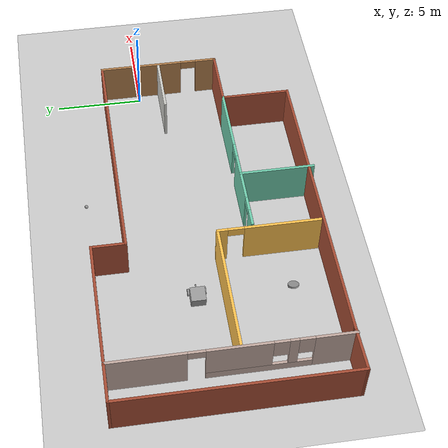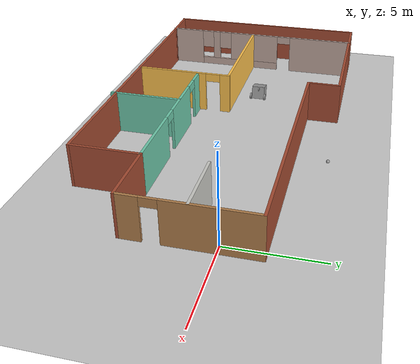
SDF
<sdf version="1.7">
 <world name="default">
  <plugin name="hello" filename="libhello.so"/>
  <light name="sun" type="directional">
   <pose>0 0 10 0 -0 0</pose>
   <diffuse>0.8 0.8 0.8 1</diffuse>
   <specular>0.2 0.2 0.2 1</specular>
   <attenuation>
    <range>1000</range>
    <constant>0.9</constant>
    <linear>0.01</linear>
    <quadratic>0.001</quadratic>
   </attenuation>
   <direction>-0.5 0.1 -0.9</direction>
   <spot><inner_angle>0</inner_angle><outer_angle>0</outer_angle><falloff>0</falloff></spot>
  </light>
  <model name="ground_plane">
   <static>1</static>
   <link name="link">
    <collision name="collision">
     <geometry><plane><normal>0 0 1</normal><size>100 100</size></plane></geometry>
     <surface><friction><ode><mu>100</mu><mu2>50</mu2></ode></friction></surface>
    </collision>
    <visual name="visual">
     <cast_shadows>0</cast_shadows>
     <geometry><plane><normal>0 0 1</normal><size>100 100</size></plane></geometry>
     <material>
      <script><uri>file://media/materials/scripts/gazebo.material</uri><name>Gazebo/Grey</name></script>
     </material>
    </visual>
   </link>
  </model>
  <gravity>0 0 -9.8</gravity>
  <magnetic_field>6e-06 2.3e-05 -4.2e-05</magnetic_field>
  <atmosphere type="adiabatic"/>
  <physics type="ode">
   <max_step_size>0.001</max_step_size>
   <real_time_factor>1</real_time_factor>
   <real_time_update_rate>1000</real_time_update_rate>
  </physics>
  <scene><ambient>0.4 0.4 0.4 1</ambient><background>0.7 0.7 0.7 1</background><shadows>1</shadows></scene>
  <spherical_coordinates>
   <surface_model>EARTH_WGS84</surface_model>
   <latitude_deg>0</latitude_deg>
   <longitude_deg>0</longitude_deg>
   <elevation>0</elevation>
   <heading_deg>0</heading_deg>
  </spherical_coordinates>
  <model name="MYROBOT">
   <link name="link_0">
    <inertial>
     <mass>1</mass>
     <inertia><ixx>0.145833</ixx><ixy>0</ixy><ixz>0</ixz><iyy>0.145833</iyy><iyz>0</iyz><izz>0.125</izz></inertia>
    </inertial>
    <pose>-0.185855 -0.46461 -0.074972 1.57 -0 0</pose>
    <visual name="visual">
     <geometry><cylinder><radius>0.2</radius><length>0.1</length></cylinder></geometry>
     <material>
      <lighting>1</lighting>
      <script><uri>file://media/materials/scripts/gazebo.material</uri><name>Gazebo/Grey</name></script>
      <shader type="pixel"><normal_map>__default__</normal_map></shader>
      <ambient>0.3 0.3 0.3 1</ambient>
      <diffuse>0.7 0.7 0.7 1</diffuse>
      <specular>0.01 0.01 0.01 1</specular>
      <emissive>0 0 0 1</emissive>
     </material>
    </visual>
    <collision name="collision">
     <geometry><cylinder><radius>0.2</radius><length>0.1</length></cylinder></geometry>
     <surface>
      <friction>
       <ode><mu>1</mu><mu2>1</mu2><fdir1>0 0 0</fdir1><slip1>0</slip1><slip2>0</slip2></ode>
       <torsional>
        <coefficient>1</coefficient>
        <patch_radius>0</patch_radius>
        <surface_radius>0</surface_radius>
        <use_patch_radius>1</use_patch_radius>
        <ode><slip>0</slip></ode>
       </torsional>
      </friction>
      <bounce><restitution_coefficient>0</restitution_coefficient><threshold>1e+06</threshold></bounce>
      <contact>
       <collide_without_contact>0</collide_without_contact>
       <collide_without_contact_bitmask>1</collide_without_contact_bitmask>
       <collide_bitmask>1</collide_bitmask>
       <ode>
        <soft_cfm>0</soft_cfm>
        <soft_erp>0.2</soft_erp>
        <kp>1e+13</kp>
        <kd>1</kd>
        <max_vel>0.01</max_vel>
        <min_depth>0</min_depth>
       </ode>
       <bullet>
        <split_impulse>1</split_impulse>
        <split_impulse_penetration_threshold>-0.01</split_impulse_penetration_threshold>
        <soft_cfm>0</soft_cfm>
        <soft_erp>0.2</soft_erp>
        <kp>1e+13</kp>
        <kd>1</kd>
       </bullet>
      </contact>
     </surface>
    </collision>
   </link>
   <link name="link_0_clone">
    <inertial>
     <mass>1</mass>
     <inertia><ixx>0.145833</ixx><ixy>0</ixy><ixz>0</ixz><iyy>0.145833</iyy><iyz>0</iyz><izz>0.125</izz></inertia>
    </inertial>
    <pose>-0.185855 0.43603 -0.074972 1.57 0 3.14</pose>
    <visual name="visual">
     <geometry><cylinder><radius>0.2</radius><length>0.1</length></cylinder></geometry>
     <material>
      <lighting>1</lighting>
      <script><uri>file://media/materials/scripts/gazebo.material</uri><name>Gazebo/Grey</name></script>
      <shader type="pixel"><normal_map>__default__</normal_map></shader>
      <ambient>0.3 0.3 0.3 1</ambient>
      <diffuse>0.7 0.7 0.7 1</diffuse>
      <specular>0.01 0.01 0.01 1</specular>
      <emissive>0 0 0 1</emissive>
     </material>
    </visual>
    <collision name="collision">
     <geometry><cylinder><radius>0.2</radius><length>0.1</length></cylinder></geometry>
     <surface>
      <friction>
       <ode><mu>1</mu><mu2>1</mu2><fdir1>0 0 0</fdir1><slip1>0</slip1><slip2>0</slip2></ode>
       <torsional>
        <coefficient>1</coefficient>
        <patch_radius>0</patch_radius>
        <surface_radius>0</surface_radius>
        <use_patch_radius>1</use_patch_radius>
        <ode><slip>0</slip></ode>
       </torsional>
      </friction>
      <bounce><restitution_coefficient>0</restitution_coefficient><threshold>1e+06</threshold></bounce>
      <contact>
       <collide_without_contact>0</collide_without_contact>
       <collide_without_contact_bitmask>1</collide_without_contact_bitmask>
       <collide_bitmask>1</collide_bitmask>
       <ode>
        <soft_cfm>0</soft_cfm>
        <soft_erp>0.2</soft_erp>
        <kp>1e+13</kp>
        <kd>1</kd>
        <max_vel>0.01</max_vel>
        <min_depth>0</min_depth>
       </ode>
       <bullet>
        <split_impulse>1</split_impulse>
        <split_impulse_penetration_threshold>-0.01</split_impulse_penetration_threshold>
        <soft_cfm>0</soft_cfm>
        <soft_erp>0.2</soft_erp>
        <kp>1e+13</kp>
        <kd>1</kd>
       </bullet>
      </contact>
     </surface>
    </collision>
   </link>
   <link name="link_1">
    <inertial>
     <mass>1</mass>
     <inertia>
      <ixx>0.166667</ixx>
      <ixy>0</ixy>
      <ixz>0</ixz>
      <iyy>0.166667</iyy>
      <iyz>0</iyz>
      <izz>0.166667</izz>
     </inertia>
    </inertial>
    <pose>0.055965 -0.01445 0.325028 0 -0 0</pose>
    <visual name="visual">
     <geometry><box><size>0.8 0.8 0.8</size></box></geometry>
     <material>
      <lighting>1</lighting>
      <script><uri>file://media/materials/scripts/gazebo.material</uri><name>Gazebo/Grey</name></script>
      <shader type="pixel"><normal_map>__default__</normal_map></shader>
      <ambient>0.3 0.3 0.3 1</ambient>
      <diffuse>0.7 0.7 0.7 1</diffuse>
      <specular>0.01 0.01 0.01 1</specular>
      <emissive>0 0 0 1</emissive>
     </material>
    </visual>
    <collision name="collision">
     <geometry><box><size>0.8 0.8 0.8</size></box></geometry>
     <surface>
      <friction>
       <ode><mu>1</mu><mu2>1</mu2><fdir1>0 0 0</fdir1><slip1>0</slip1><slip2>0</slip2></ode>
       <torsional>
        <coefficient>1</coefficient>
        <patch_radius>0</patch_radius>
        <surface_radius>0</surface_radius>
        <use_patch_radius>1</use_patch_radius>
        <ode><slip>0</slip></ode>
       </torsional>
      </friction>
      <bounce><restitution_coefficient>0</restitution_coefficient><threshold>1e+06</threshold></bounce>
      <contact>
       <collide_without_contact>0</collide_without_contact>
       <collide_without_contact_bitmask>1</collide_without_contact_bitmask>
       <collide_bitmask>1</collide_bitmask>
       <ode>
        <soft_cfm>0</soft_cfm>
        <soft_erp>0.2</soft_erp>
        <kp>1e+13</kp>
        <kd>1</kd>
        <max_vel>0.01</max_vel>
        <min_depth>0</min_depth>
       </ode>
       <bullet>
        <split_impulse>1</split_impulse>
        <split_impulse_penetration_threshold>-0.01</split_impulse_penetration_threshold>
        <soft_cfm>0</soft_cfm>
        <soft_erp>0.2</soft_erp>
        <kp>1e+13</kp>
        <kd>1</kd>
       </bullet>
      </contact>
     </surface>
    </collision>
   </link>
   <link name="link_2">
    <inertial>
     <mass>1</mass>
     <inertia><ixx>0.145833</ixx><ixy>0</ixy><ixz>0</ixz><iyy>0.145833</iyy><iyz>0</iyz><izz>0.125</izz></inertia>
    </inertial>
    <pose>0.315741 0.043034 -0.175084 1.56989 1.57 -9.7e-05</pose>
    <visual name="visual">
     <geometry><cylinder><radius>0.1</radius><length>0.05</length></cylinder></geometry>
     <material>
      <lighting>1</lighting>
      <script><uri>file://media/materials/scripts/gazebo.material</uri><name>Gazebo/Grey</name></script>
      <shader type="pixel"><normal_map>__default__</normal_map></shader>
      <ambient>0.3 0.3 0.3 1</ambient>
      <diffuse>0.7 0.7 0.7 1</diffuse>
      <specular>0.01 0.01 0.01 1</specular>
      <emissive>0 0 0 1</emissive>
     </material>
    </visual>
    <collision name="collision">
     <geometry><cylinder><radius>0.1</radius><length>0.05</length></cylinder></geometry>
     <surface>
      <friction>
       <ode><mu>1</mu><mu2>1</mu2><fdir1>0 0 0</fdir1><slip1>0</slip1><slip2>0</slip2></ode>
       <torsional>
        <coefficient>1</coefficient>
        <patch_radius>0</patch_radius>
        <surface_radius>0</surface_radius>
        <use_patch_radius>1</use_patch_radius>
        <ode><slip>0</slip></ode>
       </torsional>
      </friction>
      <bounce><restitution_coefficient>0</restitution_coefficient><threshold>1e+06</threshold></bounce>
      <contact>
       <collide_without_contact>0</collide_without_contact>
       <collide_without_contact_bitmask>1</collide_without_contact_bitmask>
       <collide_bitmask>1</collide_bitmask>
       <ode>
        <soft_cfm>0</soft_cfm>
        <soft_erp>0.2</soft_erp>
        <kp>1e+13</kp>
        <kd>1</kd>
        <max_vel>0.01</max_vel>
        <min_depth>0</min_depth>
       </ode>
       <bullet>
        <split_impulse>1</split_impulse>
        <split_impulse_penetration_threshold>-0.01</split_impulse_penetration_threshold>
        <soft_cfm>0</soft_cfm>
        <soft_erp>0.2</soft_erp>
        <kp>1e+13</kp>
        <kd>1</kd>
       </bullet>
      </contact>
     </surface>
    </collision>
   </link>
   <joint name="link_1_JOINT_0" type="revolute">
    <parent>link_1</parent>
    <child>link_0_clone</child>
    <axis>
     <xyz>0 0 1</xyz>
     <limit>
      <lower>-1.79769e+308</lower>
      <upper>1.79769e+308</upper>
      <effort>-1</effort>
      <velocity>-1</velocity>
     </limit>
     <dynamics>
      <spring_reference>0</spring_reference>
      <spring_stiffness>0</spring_stiffness>
      <damping>0</damping>
      <friction>0</friction>
     </dynamics>
    </axis>
    <physics>
     <ode><limit><cfm>0</cfm><erp>0.2</erp></limit><suspension><cfm>0</cfm><erp>0.2</erp></suspension></ode>
    </physics>
   </joint>
   <joint name="link_1_JOINT_1" type="revolute">
    <parent>link_1</parent>
    <child>link_0</child>
    <axis>
     <xyz>0 0 1</xyz>
     <limit>
      <lower>-1.79769e+308</lower>
      <upper>1.79769e+308</upper>
      <effort>-1</effort>
      <velocity>-1</velocity>
     </limit>
     <dynamics>
      <spring_reference>0</spring_reference>
      <spring_stiffness>0</spring_stiffness>
      <damping>0</damping>
      <friction>0</friction>
     </dynamics>
    </axis>
    <physics>
     <ode><limit><cfm>0</cfm><erp>0.2</erp></limit><suspension><cfm>0</cfm><erp>0.2</erp></suspension></ode>
    </physics>
   </joint>
   <joint name="link_1_JOINT_2" type="revolute">
    <parent>link_1</parent>
    <child>link_2</child>
    <axis>
     <xyz>0 0 1</xyz>
     <limit>
      <lower>-1.79769e+308</lower>
      <upper>1.79769e+308</upper>
      <effort>-1</effort>
      <velocity>-1</velocity>
     </limit>
     <dynamics>
      <spring_reference>0</spring_reference>
      <spring_stiffness>0</spring_stiffness>
      <damping>0</damping>
      <friction>0</friction>
     </dynamics>
    </axis>
    <physics>
     <ode><limit><cfm>0</cfm><erp>0.2</erp></limit><suspension><cfm>0</cfm><erp>0.2</erp></suspension></ode>
    </physics>
   </joint>
   <static>0</static>
   <pose>-14.9687 -1.3052 0.36709 -3.13675 -1.37295 3.13433</pose>
  </model>
  <model name="myhouse">
   <link name="Wall_0">
    <pose>-9.17421 0.100699 0 0 -0 1.5708</pose>
    <visual name="Wall_0_Visual_0">
     <pose>-5.2782 0 1.25 0 -0 0</pose>
     <geometry><box><size>2.1936 0.15 2.5</size></box></geometry>
     <material>
      <script><uri>file://media/materials/scripts/gazebo.material</uri><name>Gazebo/Grey</name></script>
      <ambient>0.760784 0.662745 0.627451 1</ambient>
      <shader type="pixel"/>
     </material>
     <meta><layer>0</layer></meta>
    </visual>
    <visual name="Wall_0_Visual_1">
     <pose>4.2818 0 1.25 0 -0 0</pose>
     <geometry><box><size>4.1864 0.15 2.5</size></box></geometry>
     <material>
      <script><uri>file://media/materials/scripts/gazebo.material</uri><name>Gazebo/Grey</name></script>
      <ambient>0.760784 0.662745 0.627451 1</ambient>
      <shader type="pixel"/>
     </material>
     <meta><layer>0</layer></meta>
    </visual>
    <visual name="Wall_0_Visual_2">
     <pose>-1.4464 0 0.25 0 -0 0</pose>
     <geometry><box><size>5.47 0.15 0.5</size></box></geometry>
     <material>
      <script><uri>file://media/materials/scripts/gazebo.material</uri><name>Gazebo/Grey</name></script>
      <ambient>0.760784 0.662745 0.627451 1</ambient>
      <shader type="pixel"/>
     </material>
     <meta><layer>0</layer></meta>
    </visual>
    <visual name="Wall_0_Visual_3">
     <pose>-3.14315 0 1.5 0 -0 0</pose>
     <geometry><box><size>0.4765 0.15 2</size></box></geometry>
     <material>
      <script><uri>file://media/materials/scripts/gazebo.material</uri><name>Gazebo/Grey</name></script>
      <ambient>0.760784 0.662745 0.627451 1</ambient>
      <shader type="pixel"/>
     </material>
     <meta><layer>0</layer></meta>
    </visual>
    <visual name="Wall_0_Visual_4">
     <pose>-0.408149 0 1.5 0 -0 0</pose>
     <geometry><box><size>3.3935 0.15 2</size></box></geometry>
     <material>
      <script><uri>file://media/materials/scripts/gazebo.material</uri><name>Gazebo/Grey</name></script>
      <ambient>0.760784 0.662745 0.627451 1</ambient>
      <shader type="pixel"/>
     </material>
     <meta><layer>0</layer></meta>
    </visual>
    <visual name="Wall_0_Visual_5">
     <pose>-3.7814 0 1.9 0 -0 0</pose>
     <geometry><box><size>0.8 0.15 1.2</size></box></geometry>
     <material>
      <script><uri>file://media/materials/scripts/gazebo.material</uri><name>Gazebo/Grey</name></script>
      <ambient>0.760784 0.662745 0.627451 1</ambient>
      <shader type="pixel"/>
     </material>
     <meta><layer>0</layer></meta>
    </visual>
    <visual name="Wall_0_Visual_6">
     <pose>-2.5049 0 1.9 0 -0 0</pose>
     <geometry><box><size>0.8 0.15 1.2</size></box></geometry>
     <material>
      <script><uri>file://media/materials/scripts/gazebo.material</uri><name>Gazebo/Grey</name></script>
      <ambient>0.760784 0.662745 0.627451 1</ambient>
      <shader type="pixel"/>
     </material>
     <meta><layer>0</layer></meta>
    </visual>
    <visual name="Wall_0_Visual_7">
     <pose>1.7386 0 2.25 0 -0 0</pose>
     <geometry><box><size>0.9 0.15 0.5</size></box></geometry>
     <material>
      <script><uri>file://media/materials/scripts/gazebo.material</uri><name>Gazebo/Grey</name></script>
      <ambient>0.760784 0.662745 0.627451 1</ambient>
      <shader type="pixel"/>
     </material>
     <meta><layer>0</layer></meta>
    </visual>
    <collision name="Wall_0_Collision_0">
     <pose>-5.2782 0 1.25 0 -0 0</pose>
     <geometry><box><size>2.1936 0.15 2.5</size></box></geometry>
     <surface>
      <friction>
       <ode><mu>1</mu><mu2>1</mu2><fdir1>0 0 0</fdir1><slip1>0</slip1><slip2>0</slip2></ode>
       <torsional>
        <coefficient>1</coefficient>
        <patch_radius>0</patch_radius>
        <surface_radius>0</surface_radius>
        <use_patch_radius>1</use_patch_radius>
        <ode><slip>0</slip></ode>
       </torsional>
      </friction>
      <bounce><restitution_coefficient>0</restitution_coefficient><threshold>1e+06</threshold></bounce>
      <contact>
       <collide_without_contact>0</collide_without_contact>
       <collide_without_contact_bitmask>1</collide_without_contact_bitmask>
       <collide_bitmask>1</collide_bitmask>
       <ode>
        <soft_cfm>0</soft_cfm>
        <soft_erp>0.2</soft_erp>
        <kp>1e+13</kp>
        <kd>1</kd>
        <max_vel>0.01</max_vel>
        <min_depth>0</min_depth>
       </ode>
       <bullet>
        <split_impulse>1</split_impulse>
        <split_impulse_penetration_threshold>-0.01</split_impulse_penetration_threshold>
        <soft_cfm>0</soft_cfm>
        <soft_erp>0.2</soft_erp>
        <kp>1e+13</kp>
        <kd>1</kd>
       </bullet>
      </contact>
     </surface>
    </collision>
    <collision name="Wall_0_Collision_1">
     <pose>4.2818 0 1.25 0 -0 0</pose>
     <geometry><box><size>4.1864 0.15 2.5</size></box></geometry>
     <surface>
      <friction>
       <ode><mu>1</mu><mu2>1</mu2><fdir1>0 0 0</fdir1><slip1>0</slip1><slip2>0</slip2></ode>
       <torsional>
        <coefficient>1</coefficient>
        <patch_radius>0</patch_radius>
        <surface_radius>0</surface_radius>
        <use_patch_radius>1</use_patch_radius>
        <ode><slip>0</slip></ode>
       </torsional>
      </friction>
      <bounce><restitution_coefficient>0</restitution_coefficient><threshold>1e+06</threshold></bounce>
      <contact>
       <collide_without_contact>0</collide_without_contact>
       <collide_without_contact_bitmask>1</collide_without_contact_bitmask>
       <collide_bitmask>1</collide_bitmask>
       <ode>
        <soft_cfm>0</soft_cfm>
        <soft_erp>0.2</soft_erp>
        <kp>1e+13</kp>
        <kd>1</kd>
        <max_vel>0.01</max_vel>
        <min_depth>0</min_depth>
       </ode>
       <bullet>
        <split_impulse>1</split_impulse>
        <split_impulse_penetration_threshold>-0.01</split_impulse_penetration_threshold>
        <soft_cfm>0</soft_cfm>
        <soft_erp>0.2</soft_erp>
        <kp>1e+13</kp>
        <kd>1</kd>
       </bullet>
      </contact>
     </surface>
    </collision>
    <collision name="Wall_0_Collision_2">
     <pose>-1.4464 0 0.25 0 -0 0</pose>
     <geometry><box><size>5.47 0.15 0.5</size></box></geometry>
     <surface>
      <friction>
       <ode><mu>1</mu><mu2>1</mu2><fdir1>0 0 0</fdir1><slip1>0</slip1><slip2>0</slip2></ode>
       <torsional>
        <coefficient>1</coefficient>
        <patch_radius>0</patch_radius>
        <surface_radius>0</surface_radius>
        <use_patch_radius>1</use_patch_radius>
        <ode><slip>0</slip></ode>
       </torsional>
      </friction>
      <bounce><restitution_coefficient>0</restitution_coefficient><threshold>1e+06</threshold></bounce>
      <contact>
       <collide_without_contact>0</collide_without_contact>
       <collide_without_contact_bitmask>1</collide_without_contact_bitmask>
       <collide_bitmask>1</collide_bitmask>
       <ode>
        <soft_cfm>0</soft_cfm>
        <soft_erp>0.2</soft_erp>
        <kp>1e+13</kp>
        <kd>1</kd>
        <max_vel>0.01</max_vel>
        <min_depth>0</min_depth>
       </ode>
       <bullet>
        <split_impulse>1</split_impulse>
        <split_impulse_penetration_threshold>-0.01</split_impulse_penetration_threshold>
        <soft_cfm>0</soft_cfm>
        <soft_erp>0.2</soft_erp>
        <kp>1e+13</kp>
        <kd>1</kd>
       </bullet>
      </contact>
     </surface>
    </collision>
    <collision name="Wall_0_Collision_4">
     <pose>-0.408149 0 1.5 0 -0 0</pose>
     <geometry><box><size>3.3935 0.15 2</size></box></geometry>
     <surface>
      <friction>
       <ode><mu>1</mu><mu2>1</mu2><fdir1>0 0 0</fdir1><slip1>0</slip1><slip2>0</slip2></ode>
       <torsional>
        <coefficient>1</coefficient>
        <patch_radius>0</patch_radius>
        <surface_radius>0</surface_radius>
        <use_patch_radius>1</use_patch_radius>
        <ode><slip>0</slip></ode>
       </torsional>
      </friction>
      <bounce><restitution_coefficient>0</restitution_coefficient><threshold>1e+06</threshold></bounce>
      <contact>
       <collide_without_contact>0</collide_without_contact>
       <collide_without_contact_bitmask>1</collide_without_contact_bitmask>
       <collide_bitmask>1</collide_bitmask>
       <ode>
        <soft_cfm>0</soft_cfm>
        <soft_erp>0.2</soft_erp>
        <kp>1e+13</kp>
        <kd>1</kd>
        <max_vel>0.01</max_vel>
        <min_depth>0</min_depth>
       </ode>
       <bullet>
        <split_impulse>1</split_impulse>
        <split_impulse_penetration_threshold>-0.01</split_impulse_penetration_threshold>
        <soft_cfm>0</soft_cfm>
        <soft_erp>0.2</soft_erp>
        <kp>1e+13</kp>
        <kd>1</kd>
       </bullet>
      </contact>
     </surface>
    </collision>
    <collision name="Wall_0_Collision_3">
     <pose>-3.14315 0 1.5 0 -0 0</pose>
     <geometry><box><size>0.4765 0.15 2</size></box></geometry>
     <surface>
      <friction>
       <ode><mu>1</mu><mu2>1</mu2><fdir1>0 0 0</fdir1><slip1>0</slip1><slip2>0</slip2></ode>
       <torsional>
        <coefficient>1</coefficient>
        <patch_radius>0</patch_radius>
        <surface_radius>0</surface_radius>
        <use_patch_radius>1</use_patch_radius>
        <ode><slip>0</slip></ode>
       </torsional>
      </friction>
      <bounce><restitution_coefficient>0</restitution_coefficient><threshold>1e+06</threshold></bounce>
      <contact>
       <collide_without_contact>0</collide_without_contact>
       <collide_without_contact_bitmask>1</collide_without_contact_bitmask>
       <collide_bitmask>1</collide_bitmask>
       <ode>
        <soft_cfm>0</soft_cfm>
        <soft_erp>0.2</soft_erp>
        <kp>1e+13</kp>
        <kd>1</kd>
        <max_vel>0.01</max_vel>
        <min_depth>0</min_depth>
       </ode>
       <bullet>
        <split_impulse>1</split_impulse>
        <split_impulse_penetration_threshold>-0.01</split_impulse_penetration_threshold>
        <soft_cfm>0</soft_cfm>
        <soft_erp>0.2</soft_erp>
        <kp>1e+13</kp>
        <kd>1</kd>
       </bullet>
      </contact>
     </surface>
    </collision>
    <collision name="Wall_0_Collision_5">
     <pose>-3.7814 0 1.9 0 -0 0</pose>
     <geometry><box><size>0.8 0.15 1.2</size></box></geometry>
     <surface>
      <friction>
       <ode><mu>1</mu><mu2>1</mu2><fdir1>0 0 0</fdir1><slip1>0</slip1><slip2>0</slip2></ode>
       <torsional>
        <coefficient>1</coefficient>
        <patch_radius>0</patch_radius>
        <surface_radius>0</surface_radius>
        <use_patch_radius>1</use_patch_radius>
        <ode><slip>0</slip></ode>
       </torsional>
      </friction>
      <bounce><restitution_coefficient>0</restitution_coefficient><threshold>1e+06</threshold></bounce>
      <contact>
       <collide_without_contact>0</collide_without_contact>
       <collide_without_contact_bitmask>1</collide_without_contact_bitmask>
       <collide_bitmask>1</collide_bitmask>
       <ode>
        <soft_cfm>0</soft_cfm>
        <soft_erp>0.2</soft_erp>
        <kp>1e+13</kp>
        <kd>1</kd>
        <max_vel>0.01</max_vel>
        <min_depth>0</min_depth>
       </ode>
       <bullet>
        <split_impulse>1</split_impulse>
        <split_impulse_penetration_threshold>-0.01</split_impulse_penetration_threshold>
        <soft_cfm>0</soft_cfm>
        <soft_erp>0.2</soft_erp>
        <kp>1e+13</kp>
        <kd>1</kd>
       </bullet>
      </contact>
     </surface>
    </collision>
    <collision name="Wall_0_Collision_6">
     <pose>-2.5049 0 1.9 0 -0 0</pose>
     <geometry><box><size>0.8 0.15 1.2</size></box></geometry>
     <surface>
      <friction>
       <ode><mu>1</mu><mu2>1</mu2><fdir1>0 0 0</fdir1><slip1>0</slip1><slip2>0</slip2></ode>
       <torsional>
        <coefficient>1</coefficient>
        <patch_radius>0</patch_radius>
        <surface_radius>0</surface_radius>
        <use_patch_radius>1</use_patch_radius>
        <ode><slip>0</slip></ode>
       </torsional>
      </friction>
      <bounce><restitution_coefficient>0</restitution_coefficient><threshold>1e+06</threshold></bounce>
      <contact>
       <collide_without_contact>0</collide_without_contact>
       <collide_without_contact_bitmask>1</collide_without_contact_bitmask>
       <collide_bitmask>1</collide_bitmask>
       <ode>
        <soft_cfm>0</soft_cfm>
        <soft_erp>0.2</soft_erp>
        <kp>1e+13</kp>
        <kd>1</kd>
        <max_vel>0.01</max_vel>
        <min_depth>0</min_depth>
       </ode>
       <bullet>
        <split_impulse>1</split_impulse>
        <split_impulse_penetration_threshold>-0.01</split_impulse_penetration_threshold>
        <soft_cfm>0</soft_cfm>
        <soft_erp>0.2</soft_erp>
        <kp>1e+13</kp>
        <kd>1</kd>
       </bullet>
      </contact>
     </surface>
    </collision>
    <collision name="Wall_0_Collision_7">
     <pose>1.7386 0 2.25 0 -0 0</pose>
     <geometry><box><size>0.9 0.15 0.5</size></box></geometry>
     <surface>
      <friction>
       <ode><mu>1</mu><mu2>1</mu2><fdir1>0 0 0</fdir1><slip1>0</slip1><slip2>0</slip2></ode>
       <torsional>
        <coefficient>1</coefficient>
        <patch_radius>0</patch_radius>
        <surface_radius>0</surface_radius>
        <use_patch_radius>1</use_patch_radius>
        <ode><slip>0</slip></ode>
       </torsional>
      </friction>
      <bounce><restitution_coefficient>0</restitution_coefficient><threshold>1e+06</threshold></bounce>
      <contact>
       <collide_without_contact>0</collide_without_contact>
       <collide_without_contact_bitmask>1</collide_without_contact_bitmask>
       <collide_bitmask>1</collide_bitmask>
       <ode>
        <soft_cfm>0</soft_cfm>
        <soft_erp>0.2</soft_erp>
        <kp>1e+13</kp>
        <kd>1</kd>
        <max_vel>0.01</max_vel>
        <min_depth>0</min_depth>
       </ode>
       <bullet>
        <split_impulse>1</split_impulse>
        <split_impulse_penetration_threshold>-0.01</split_impulse_penetration_threshold>
        <soft_cfm>0</soft_cfm>
        <soft_erp>0.2</soft_erp>
        <kp>1e+13</kp>
        <kd>1</kd>
       </bullet>
      </contact>
     </surface>
    </collision>
   </link>
   <link name="Wall_1">
    <pose>-5.62421 6.4007 0 0 -0 0</pose>
    <visual name="Wall_1_Visual">
     <pose>0 0 1.25 0 -0 0</pose>
     <geometry><box><size>7.25 0.15 2.5</size></box></geometry>
     <material>
      <script><uri>file://media/materials/scripts/gazebo.material</uri><name>Gazebo/Bricks</name></script>
      <ambient>1 1 1 1</ambient>
      <shader type="pixel"/>
     </material>
     <meta><layer>0</layer></meta>
    </visual>
    <collision name="Wall_1_Collision">
     <pose>0 0 1.25 0 -0 0</pose>
     <geometry><box><size>7.25 0.15 2.5</size></box></geometry>
     <surface>
      <friction>
       <ode><mu>1</mu><mu2>1</mu2><fdir1>0 0 0</fdir1><slip1>0</slip1><slip2>0</slip2></ode>
       <torsional>
        <coefficient>1</coefficient>
        <patch_radius>0</patch_radius>
        <surface_radius>0</surface_radius>
        <use_patch_radius>1</use_patch_radius>
        <ode><slip>0</slip></ode>
       </torsional>
      </friction>
      <bounce><restitution_coefficient>0</restitution_coefficient><threshold>1e+06</threshold></bounce>
      <contact>
       <collide_without_contact>0</collide_without_contact>
       <collide_without_contact_bitmask>1</collide_without_contact_bitmask>
       <collide_bitmask>1</collide_bitmask>
       <ode>
        <soft_cfm>0</soft_cfm>
        <soft_erp>0.2</soft_erp>
        <kp>1e+13</kp>
        <kd>1</kd>
        <max_vel>0.01</max_vel>
        <min_depth>0</min_depth>
       </ode>
       <bullet>
        <split_impulse>1</split_impulse>
        <split_impulse_penetration_threshold>-0.01</split_impulse_penetration_threshold>
        <soft_cfm>0</soft_cfm>
        <soft_erp>0.2</soft_erp>
        <kp>1e+13</kp>
        <kd>1</kd>
       </bullet>
      </contact>
     </surface>
    </collision>
   </link>
   <link name="Wall_10">
    <pose>-1.92135 -3.16828 0 0 0 -1.5708</pose>
    <visual name="Wall_10_Visual_1">
     <pose>0.76296 0 1.25 0 -0 0</pose>
     <geometry><box><size>4.22408 0.15 2.5</size></box></geometry>
     <material>
      <script><uri>file://media/materials/scripts/gazebo.material</uri><name>Gazebo/Grey</name></script>
      <ambient>1 0.764706 0.305882 1</ambient>
      <shader type="pixel"/>
     </material>
     <meta><layer>0</layer></meta>
    </visual>
    <visual name="Wall_10_Visual_0">
     <pose>-2.56204 0 1.25 0 -0 0</pose>
     <geometry><box><size>0.62592 0.15 2.5</size></box></geometry>
     <material>
      <script><uri>file://media/materials/scripts/gazebo.material</uri><name>Gazebo/Grey</name></script>
      <ambient>1 0.764706 0.305882 1</ambient>
      <shader type="pixel"/>
     </material>
     <meta><layer>0</layer></meta>
    </visual>
    <visual name="Wall_10_Visual_2">
     <pose>-1.79908 0 2.25 0 -0 0</pose>
     <geometry><box><size>0.9 0.15 0.5</size></box></geometry>
     <material>
      <script><uri>file://media/materials/scripts/gazebo.material</uri><name>Gazebo/Grey</name></script>
      <ambient>1 0.764706 0.305882 1</ambient>
      <shader type="pixel"/>
     </material>
     <meta><layer>0</layer></meta>
    </visual>
    <collision name="Wall_10_Collision_0">
     <pose>-2.56204 0 1.25 0 -0 0</pose>
     <geometry><box><size>0.62592 0.15 2.5</size></box></geometry>
     <surface>
      <friction>
       <ode><mu>1</mu><mu2>1</mu2><fdir1>0 0 0</fdir1><slip1>0</slip1><slip2>0</slip2></ode>
       <torsional>
        <coefficient>1</coefficient>
        <patch_radius>0</patch_radius>
        <surface_radius>0</surface_radius>
        <use_patch_radius>1</use_patch_radius>
        <ode><slip>0</slip></ode>
       </torsional>
      </friction>
      <bounce><restitution_coefficient>0</restitution_coefficient><threshold>1e+06</threshold></bounce>
      <contact>
       <collide_without_contact>0</collide_without_contact>
       <collide_without_contact_bitmask>1</collide_without_contact_bitmask>
       <collide_bitmask>1</collide_bitmask>
       <ode>
        <soft_cfm>0</soft_cfm>
        <soft_erp>0.2</soft_erp>
        <kp>1e+13</kp>
        <kd>1</kd>
        <max_vel>0.01</max_vel>
        <min_depth>0</min_depth>
       </ode>
       <bullet>
        <split_impulse>1</split_impulse>
        <split_impulse_penetration_threshold>-0.01</split_impulse_penetration_threshold>
        <soft_cfm>0</soft_cfm>
        <soft_erp>0.2</soft_erp>
        <kp>1e+13</kp>
        <kd>1</kd>
       </bullet>
      </contact>
     </surface>
    </collision>
    <collision name="Wall_10_Collision_1">
     <pose>0.76296 0 1.25 0 -0 0</pose>
     <geometry><box><size>4.22408 0.15 2.5</size></box></geometry>
     <surface>
      <friction>
       <ode><mu>1</mu><mu2>1</mu2><fdir1>0 0 0</fdir1><slip1>0</slip1><slip2>0</slip2></ode>
       <torsional>
        <coefficient>1</coefficient>
        <patch_radius>0</patch_radius>
        <surface_radius>0</surface_radius>
        <use_patch_radius>1</use_patch_radius>
        <ode><slip>0</slip></ode>
       </torsional>
      </friction>
      <bounce><restitution_coefficient>0</restitution_coefficient><threshold>1e+06</threshold></bounce>
      <contact>
       <collide_without_contact>0</collide_without_contact>
       <collide_without_contact_bitmask>1</collide_without_contact_bitmask>
       <collide_bitmask>1</collide_bitmask>
       <ode>
        <soft_cfm>0</soft_cfm>
        <soft_erp>0.2</soft_erp>
        <kp>1e+13</kp>
        <kd>1</kd>
        <max_vel>0.01</max_vel>
        <min_depth>0</min_depth>
       </ode>
       <bullet>
        <split_impulse>1</split_impulse>
        <split_impulse_penetration_threshold>-0.01</split_impulse_penetration_threshold>
        <soft_cfm>0</soft_cfm>
        <soft_erp>0.2</soft_erp>
        <kp>1e+13</kp>
        <kd>1</kd>
       </bullet>
      </contact>
     </surface>
    </collision>
    <collision name="Wall_10_Collision_2">
     <pose>-1.79908 0 2.25 0 -0 0</pose>
     <geometry><box><size>0.9 0.15 0.5</size></box></geometry>
     <surface>
      <friction>
       <ode><mu>1</mu><mu2>1</mu2><fdir1>0 0 0</fdir1><slip1>0</slip1><slip2>0</slip2></ode>
       <torsional>
        <coefficient>1</coefficient>
        <patch_radius>0</patch_radius>
        <surface_radius>0</surface_radius>
        <use_patch_radius>1</use_patch_radius>
        <ode><slip>0</slip></ode>
       </torsional>
      </friction>
      <bounce><restitution_coefficient>0</restitution_coefficient><threshold>1e+06</threshold></bounce>
      <contact>
       <collide_without_contact>0</collide_without_contact>
       <collide_without_contact_bitmask>1</collide_without_contact_bitmask>
       <collide_bitmask>1</collide_bitmask>
       <ode>
        <soft_cfm>0</soft_cfm>
        <soft_erp>0.2</soft_erp>
        <kp>1e+13</kp>
        <kd>1</kd>
        <max_vel>0.01</max_vel>
        <min_depth>0</min_depth>
       </ode>
       <bullet>
        <split_impulse>1</split_impulse>
        <split_impulse_penetration_threshold>-0.01</split_impulse_penetration_threshold>
        <soft_cfm>0</soft_cfm>
        <soft_erp>0.2</soft_erp>
        <kp>1e+13</kp>
        <kd>1</kd>
       </bullet>
      </contact>
     </surface>
    </collision>
   </link>
   <link name="Wall_12">
    <pose>-10.2242 6.4007 0 0 -0 3.14159</pose>
    <visual name="Wall_12_Visual">
     <pose>0 0 1.25 0 -0 0</pose>
     <geometry><box><size>2.25 0.15 2.5</size></box></geometry>
     <material>
      <script><uri>file://media/materials/scripts/gazebo.material</uri><name>Gazebo/Bricks</name></script>
      <ambient>1 1 1 1</ambient>
      <shader type="pixel"/>
     </material>
     <meta><layer>0</layer></meta>
    </visual>
    <collision name="Wall_12_Collision">
     <pose>0 0 1.25 0 -0 0</pose>
     <geometry><box><size>2.25 0.15 2.5</size></box></geometry>
     <surface>
      <friction>
       <ode><mu>1</mu><mu2>1</mu2><fdir1>0 0 0</fdir1><slip1>0</slip1><slip2>0</slip2></ode>
       <torsional>
        <coefficient>1</coefficient>
        <patch_radius>0</patch_radius>
        <surface_radius>0</surface_radius>
        <use_patch_radius>1</use_patch_radius>
        <ode><slip>0</slip></ode>
       </torsional>
      </friction>
      <bounce><restitution_coefficient>0</restitution_coefficient><threshold>1e+06</threshold></bounce>
      <contact>
       <collide_without_contact>0</collide_without_contact>
       <collide_without_contact_bitmask>1</collide_without_contact_bitmask>
       <collide_bitmask>1</collide_bitmask>
       <ode>
        <soft_cfm>0</soft_cfm>
        <soft_erp>0.2</soft_erp>
        <kp>1e+13</kp>
        <kd>1</kd>
        <max_vel>0.01</max_vel>
        <min_depth>0</min_depth>
       </ode>
       <bullet>
        <split_impulse>1</split_impulse>
        <split_impulse_penetration_threshold>-0.01</split_impulse_penetration_threshold>
        <soft_cfm>0</soft_cfm>
        <soft_erp>0.2</soft_erp>
        <kp>1e+13</kp>
        <kd>1</kd>
       </bullet>
      </contact>
     </surface>
    </collision>
   </link>
   <link name="Wall_13">
    <pose>-11.2742 0.100699 0 0 0 -1.5708</pose>
    <visual name="Wall_13_Visual">
     <pose>0 0 1.25 0 -0 0</pose>
     <geometry><box><size>12.75 0.15 2.5</size></box></geometry>
     <material>
      <script><uri>file://media/materials/scripts/gazebo.material</uri><name>Gazebo/Bricks</name></script>
      <ambient>1 1 1 1</ambient>
      <shader type="pixel"/>
     </material>
     <meta><layer>0</layer></meta>
    </visual>
    <collision name="Wall_13_Collision">
     <pose>0 0 1.25 0 -0 0</pose>
     <geometry><box><size>12.75 0.15 2.5</size></box></geometry>
     <surface>
      <friction>
       <ode><mu>1</mu><mu2>1</mu2><fdir1>0 0 0</fdir1><slip1>0</slip1><slip2>0</slip2></ode>
       <torsional>
        <coefficient>1</coefficient>
        <patch_radius>0</patch_radius>
        <surface_radius>0</surface_radius>
        <use_patch_radius>1</use_patch_radius>
        <ode><slip>0</slip></ode>
       </torsional>
      </friction>
      <bounce><restitution_coefficient>0</restitution_coefficient><threshold>1e+06</threshold></bounce>
      <contact>
       <collide_without_contact>0</collide_without_contact>
       <collide_without_contact_bitmask>1</collide_without_contact_bitmask>
       <collide_bitmask>1</collide_bitmask>
       <ode>
        <soft_cfm>0</soft_cfm>
        <soft_erp>0.2</soft_erp>
        <kp>1e+13</kp>
        <kd>1</kd>
        <max_vel>0.01</max_vel>
        <min_depth>0</min_depth>
       </ode>
       <bullet>
        <split_impulse>1</split_impulse>
        <split_impulse_penetration_threshold>-0.01</split_impulse_penetration_threshold>
        <soft_cfm>0</soft_cfm>
        <soft_erp>0.2</soft_erp>
        <kp>1e+13</kp>
        <kd>1</kd>
       </bullet>
      </contact>
     </surface>
    </collision>
   </link>
   <link name="Wall_14">
    <pose>-10.0992 -6.1743 0 0 -0 0.021273</pose>
    <visual name="Wall_14_Visual">
     <pose>0 0 1.25 0 -0 0</pose>
     <geometry><box><size>2.50053 0.15 2.5</size></box></geometry>
     <material>
      <script><uri>file://media/materials/scripts/gazebo.material</uri><name>Gazebo/Bricks</name></script>
      <ambient>1 1 1 1</ambient>
      <shader type="pixel"/>
     </material>
     <meta><layer>0</layer></meta>
    </visual>
    <collision name="Wall_14_Collision">
     <pose>0 0 1.25 0 -0 0</pose>
     <geometry><box><size>2.50053 0.15 2.5</size></box></geometry>
     <surface>
      <friction>
       <ode><mu>1</mu><mu2>1</mu2><fdir1>0 0 0</fdir1><slip1>0</slip1><slip2>0</slip2></ode>
       <torsional>
        <coefficient>1</coefficient>
        <patch_radius>0</patch_radius>
        <surface_radius>0</surface_radius>
        <use_patch_radius>1</use_patch_radius>
        <ode><slip>0</slip></ode>
       </torsional>
      </friction>
      <bounce><restitution_coefficient>0</restitution_coefficient><threshold>1e+06</threshold></bounce>
      <contact>
       <collide_without_contact>0</collide_without_contact>
       <collide_without_contact_bitmask>1</collide_without_contact_bitmask>
       <collide_bitmask>1</collide_bitmask>
       <ode>
        <soft_cfm>0</soft_cfm>
        <soft_erp>0.2</soft_erp>
        <kp>1e+13</kp>
        <kd>1</kd>
        <max_vel>0.01</max_vel>
        <min_depth>0</min_depth>
       </ode>
       <bullet>
        <split_impulse>1</split_impulse>
        <split_impulse_penetration_threshold>-0.01</split_impulse_penetration_threshold>
        <soft_cfm>0</soft_cfm>
        <soft_erp>0.2</soft_erp>
        <kp>1e+13</kp>
        <kd>1</kd>
       </bullet>
      </contact>
     </surface>
    </collision>
   </link>
   <link name="Wall_16">
    <pose>3.12579 -2.2993 0 0 -0 3.14159</pose>
    <visual name="Wall_16_Visual_0">
     <pose>-2.92576 0 1.25 0 -0 0</pose>
     <geometry><box><size>3.89848 0.15 2.5</size></box></geometry>
     <material>
      <script><uri>file://media/materials/scripts/gazebo.material</uri><name>Gazebo/Grey</name></script>
      <ambient>0.435294 0.796078 0.67451 1</ambient>
      <shader type="pixel"/>
     </material>
     <meta><layer>0</layer></meta>
    </visual>
    <visual name="Wall_16_Visual_1">
     <pose>1.45723 0 1.25 0 -0 0</pose>
     <geometry><box><size>3.0675 0.15 2.5</size></box></geometry>
     <material>
      <script><uri>file://media/materials/scripts/gazebo.material</uri><name>Gazebo/Grey</name></script>
      <ambient>0.435294 0.796078 0.67451 1</ambient>
      <shader type="pixel"/>
     </material>
     <meta><layer>0</layer></meta>
    </visual>
    <visual name="Wall_16_Visual_2">
     <pose>4.38299 0 1.25 0 -0 0</pose>
     <geometry><box><size>0.984022 0.15 2.5</size></box></geometry>
     <material>
      <script><uri>file://media/materials/scripts/gazebo.material</uri><name>Gazebo/Grey</name></script>
      <ambient>0.435294 0.796078 0.67451 1</ambient>
      <shader type="pixel"/>
     </material>
     <meta><layer>0</layer></meta>
    </visual>
    <visual name="Wall_16_Visual_3">
     <pose>-0.526522 0 2.25 0 -0 0</pose>
     <geometry><box><size>0.9 0.15 0.5</size></box></geometry>
     <material>
      <script><uri>file://media/materials/scripts/gazebo.material</uri><name>Gazebo/Grey</name></script>
      <ambient>0.435294 0.796078 0.67451 1</ambient>
      <shader type="pixel"/>
     </material>
     <meta><layer>0</layer></meta>
    </visual>
    <visual name="Wall_16_Visual_4">
     <pose>3.44098 0 2.25 0 -0 0</pose>
     <geometry><box><size>0.9 0.15 0.5</size></box></geometry>
     <material>
      <script><uri>file://media/materials/scripts/gazebo.material</uri><name>Gazebo/Grey</name></script>
      <ambient>0.435294 0.796078 0.67451 1</ambient>
      <shader type="pixel"/>
     </material>
     <meta><layer>0</layer></meta>
    </visual>
    <collision name="Wall_16_Collision_0">
     <pose>-2.92576 0 1.25 0 -0 0</pose>
     <geometry><box><size>3.89848 0.15 2.5</size></box></geometry>
     <surface>
      <friction>
       <ode><mu>1</mu><mu2>1</mu2><fdir1>0 0 0</fdir1><slip1>0</slip1><slip2>0</slip2></ode>
       <torsional>
        <coefficient>1</coefficient>
        <patch_radius>0</patch_radius>
        <surface_radius>0</surface_radius>
        <use_patch_radius>1</use_patch_radius>
        <ode><slip>0</slip></ode>
       </torsional>
      </friction>
      <bounce><restitution_coefficient>0</restitution_coefficient><threshold>1e+06</threshold></bounce>
      <contact>
       <collide_without_contact>0</collide_without_contact>
       <collide_without_contact_bitmask>1</collide_without_contact_bitmask>
       <collide_bitmask>1</collide_bitmask>
       <ode>
        <soft_cfm>0</soft_cfm>
        <soft_erp>0.2</soft_erp>
        <kp>1e+13</kp>
        <kd>1</kd>
        <max_vel>0.01</max_vel>
        <min_depth>0</min_depth>
       </ode>
       <bullet>
        <split_impulse>1</split_impulse>
        <split_impulse_penetration_threshold>-0.01</split_impulse_penetration_threshold>
        <soft_cfm>0</soft_cfm>
        <soft_erp>0.2</soft_erp>
        <kp>1e+13</kp>
        <kd>1</kd>
       </bullet>
      </contact>
     </surface>
    </collision>
    <collision name="Wall_16_Collision_1">
     <pose>1.45723 0 1.25 0 -0 0</pose>
     <geometry><box><size>3.0675 0.15 2.5</size></box></geometry>
     <surface>
      <friction>
       <ode><mu>1</mu><mu2>1</mu2><fdir1>0 0 0</fdir1><slip1>0</slip1><slip2>0</slip2></ode>
       <torsional>
        <coefficient>1</coefficient>
        <patch_radius>0</patch_radius>
        <surface_radius>0</surface_radius>
        <use_patch_radius>1</use_patch_radius>
        <ode><slip>0</slip></ode>
       </torsional>
      </friction>
      <bounce><restitution_coefficient>0</restitution_coefficient><threshold>1e+06</threshold></bounce>
      <contact>
       <collide_without_contact>0</collide_without_contact>
       <collide_without_contact_bitmask>1</collide_without_contact_bitmask>
       <collide_bitmask>1</collide_bitmask>
       <ode>
        <soft_cfm>0</soft_cfm>
        <soft_erp>0.2</soft_erp>
        <kp>1e+13</kp>
        <kd>1</kd>
        <max_vel>0.01</max_vel>
        <min_depth>0</min_depth>
       </ode>
       <bullet>
        <split_impulse>1</split_impulse>
        <split_impulse_penetration_threshold>-0.01</split_impulse_penetration_threshold>
        <soft_cfm>0</soft_cfm>
        <soft_erp>0.2</soft_erp>
        <kp>1e+13</kp>
        <kd>1</kd>
       </bullet>
      </contact>
     </surface>
    </collision>
    <collision name="Wall_16_Collision_2">
     <pose>4.38299 0 1.25 0 -0 0</pose>
     <geometry><box><size>0.984022 0.15 2.5</size></box></geometry>
     <surface>
      <friction>
       <ode><mu>1</mu><mu2>1</mu2><fdir1>0 0 0</fdir1><slip1>0</slip1><slip2>0</slip2></ode>
       <torsional>
        <coefficient>1</coefficient>
        <patch_radius>0</patch_radius>
        <surface_radius>0</surface_radius>
        <use_patch_radius>1</use_patch_radius>
        <ode><slip>0</slip></ode>
       </torsional>
      </friction>
      <bounce><restitution_coefficient>0</restitution_coefficient><threshold>1e+06</threshold></bounce>
      <contact>
       <collide_without_contact>0</collide_without_contact>
       <collide_without_contact_bitmask>1</collide_without_contact_bitmask>
       <collide_bitmask>1</collide_bitmask>
       <ode>
        <soft_cfm>0</soft_cfm>
        <soft_erp>0.2</soft_erp>
        <kp>1e+13</kp>
        <kd>1</kd>
        <max_vel>0.01</max_vel>
        <min_depth>0</min_depth>
       </ode>
       <bullet>
        <split_impulse>1</split_impulse>
        <split_impulse_penetration_threshold>-0.01</split_impulse_penetration_threshold>
        <soft_cfm>0</soft_cfm>
        <soft_erp>0.2</soft_erp>
        <kp>1e+13</kp>
        <kd>1</kd>
       </bullet>
      </contact>
     </surface>
    </collision>
    <collision name="Wall_16_Collision_3">
     <pose>-0.526522 0 2.25 0 -0 0</pose>
     <geometry><box><size>0.9 0.15 0.5</size></box></geometry>
     <surface>
      <friction>
       <ode><mu>1</mu><mu2>1</mu2><fdir1>0 0 0</fdir1><slip1>0</slip1><slip2>0</slip2></ode>
       <torsional>
        <coefficient>1</coefficient>
        <patch_radius>0</patch_radius>
        <surface_radius>0</surface_radius>
        <use_patch_radius>1</use_patch_radius>
        <ode><slip>0</slip></ode>
       </torsional>
      </friction>
      <bounce><restitution_coefficient>0</restitution_coefficient><threshold>1e+06</threshold></bounce>
      <contact>
       <collide_without_contact>0</collide_without_contact>
       <collide_without_contact_bitmask>1</collide_without_contact_bitmask>
       <collide_bitmask>1</collide_bitmask>
       <ode>
        <soft_cfm>0</soft_cfm>
        <soft_erp>0.2</soft_erp>
        <kp>1e+13</kp>
        <kd>1</kd>
        <max_vel>0.01</max_vel>
        <min_depth>0</min_depth>
       </ode>
       <bullet>
        <split_impulse>1</split_impulse>
        <split_impulse_penetration_threshold>-0.01</split_impulse_penetration_threshold>
        <soft_cfm>0</soft_cfm>
        <soft_erp>0.2</soft_erp>
        <kp>1e+13</kp>
        <kd>1</kd>
       </bullet>
      </contact>
     </surface>
    </collision>
    <collision name="Wall_16_Collision_4">
     <pose>3.44098 0 2.25 0 -0 0</pose>
     <geometry><box><size>0.9 0.15 0.5</size></box></geometry>
     <surface>
      <friction>
       <ode><mu>1</mu><mu2>1</mu2><fdir1>0 0 0</fdir1><slip1>0</slip1><slip2>0</slip2></ode>
       <torsional>
        <coefficient>1</coefficient>
        <patch_radius>0</patch_radius>
        <surface_radius>0</surface_radius>
        <use_patch_radius>1</use_patch_radius>
        <ode><slip>0</slip></ode>
       </torsional>
      </friction>
      <bounce><restitution_coefficient>0</restitution_coefficient><threshold>1e+06</threshold></bounce>
      <contact>
       <collide_without_contact>0</collide_without_contact>
       <collide_without_contact_bitmask>1</collide_without_contact_bitmask>
       <collide_bitmask>1</collide_bitmask>
       <ode>
        <soft_cfm>0</soft_cfm>
        <soft_erp>0.2</soft_erp>
        <kp>1e+13</kp>
        <kd>1</kd>
        <max_vel>0.01</max_vel>
        <min_depth>0</min_depth>
       </ode>
       <bullet>
        <split_impulse>1</split_impulse>
        <split_impulse_penetration_threshold>-0.01</split_impulse_penetration_threshold>
        <soft_cfm>0</soft_cfm>
        <soft_erp>0.2</soft_erp>
        <kp>1e+13</kp>
        <kd>1</kd>
       </bullet>
      </contact>
     </surface>
    </collision>
   </link>
   <link name="Wall_18">
    <pose>1.89281 -4.3507 0 0 0 -1.5708</pose>
    <visual name="Wall_18_Visual">
     <pose>0 0 1.25 0 -0 0</pose>
     <geometry><box><size>4.25 0.15 2.5</size></box></geometry>
     <material>
      <script><uri>file://media/materials/scripts/gazebo.material</uri><name>Gazebo/Grey</name></script>
      <ambient>0.435294 0.796078 0.67451 1</ambient>
      <shader type="pixel"/>
     </material>
     <meta><layer>0</layer></meta>
    </visual>
    <collision name="Wall_18_Collision">
     <pose>0 0 1.25 0 -0 0</pose>
     <geometry><box><size>4.25 0.15 2.5</size></box></geometry>
     <surface>
      <friction>
       <ode><mu>1</mu><mu2>1</mu2><fdir1>0 0 0</fdir1><slip1>0</slip1><slip2>0</slip2></ode>
       <torsional>
        <coefficient>1</coefficient>
        <patch_radius>0</patch_radius>
        <surface_radius>0</surface_radius>
        <use_patch_radius>1</use_patch_radius>
        <ode><slip>0</slip></ode>
       </torsional>
      </friction>
      <bounce><restitution_coefficient>0</restitution_coefficient><threshold>1e+06</threshold></bounce>
      <contact>
       <collide_without_contact>0</collide_without_contact>
       <collide_without_contact_bitmask>1</collide_without_contact_bitmask>
       <collide_bitmask>1</collide_bitmask>
       <ode>
        <soft_cfm>0</soft_cfm>
        <soft_erp>0.2</soft_erp>
        <kp>1e+13</kp>
        <kd>1</kd>
        <max_vel>0.01</max_vel>
        <min_depth>0</min_depth>
       </ode>
       <bullet>
        <split_impulse>1</split_impulse>
        <split_impulse_penetration_threshold>-0.01</split_impulse_penetration_threshold>
        <soft_cfm>0</soft_cfm>
        <soft_erp>0.2</soft_erp>
        <kp>1e+13</kp>
        <kd>1</kd>
       </bullet>
      </contact>
     </surface>
    </collision>
   </link>
   <link name="Wall_2">
    <pose>-2.07421 5.4757 0 0 0 -1.5708</pose>
    <visual name="Wall_2_Visual">
     <pose>0 0 1.25 0 -0 0</pose>
     <geometry><box><size>2 0.15 2.5</size></box></geometry>
     <material>
      <script><uri>file://media/materials/scripts/gazebo.material</uri><name>Gazebo/Bricks</name></script>
      <ambient>1 1 1 1</ambient>
      <shader type="pixel"/>
     </material>
     <meta><layer>0</layer></meta>
    </visual>
    <collision name="Wall_2_Collision">
     <pose>0 0 1.25 0 -0 0</pose>
     <geometry><box><size>2 0.15 2.5</size></box></geometry>
     <surface>
      <friction>
       <ode><mu>1</mu><mu2>1</mu2><fdir1>0 0 0</fdir1><slip1>0</slip1><slip2>0</slip2></ode>
       <torsional>
        <coefficient>1</coefficient>
        <patch_radius>0</patch_radius>
        <surface_radius>0</surface_radius>
        <use_patch_radius>1</use_patch_radius>
        <ode><slip>0</slip></ode>
       </torsional>
      </friction>
      <bounce><restitution_coefficient>0</restitution_coefficient><threshold>1e+06</threshold></bounce>
      <contact>
       <collide_without_contact>0</collide_without_contact>
       <collide_without_contact_bitmask>1</collide_without_contact_bitmask>
       <collide_bitmask>1</collide_bitmask>
       <ode>
        <soft_cfm>0</soft_cfm>
        <soft_erp>0.2</soft_erp>
        <kp>1e+13</kp>
        <kd>1</kd>
        <max_vel>0.01</max_vel>
        <min_depth>0</min_depth>
       </ode>
       <bullet>
        <split_impulse>1</split_impulse>
        <split_impulse_penetration_threshold>-0.01</split_impulse_penetration_threshold>
        <soft_cfm>0</soft_cfm>
        <soft_erp>0.2</soft_erp>
        <kp>1e+13</kp>
        <kd>1</kd>
       </bullet>
      </contact>
     </surface>
    </collision>
   </link>
   <link name="Wall_20">
    <pose>9.56731 1.1493 0 0 -0 3.14159</pose>
    <visual name="Wall_20_Visual">
     <pose>0 0 1.25 0 -0 0</pose>
     <geometry><box><size>3.5 0.15 2.5</size></box></geometry>
     <material>
      <script><uri>file://media/materials/scripts/gazebo.material</uri><name>Gazebo/CeilingTiled</name></script>
      <ambient>0.435294 0.796078 0.67451 1</ambient>
      <shader type="pixel"/>
     </material>
     <meta><layer>0</layer></meta>
    </visual>
    <collision name="Wall_20_Collision">
     <pose>0 0 1.25 0 -0 0</pose>
     <geometry><box><size>3.5 0.15 2.5</size></box></geometry>
     <surface>
      <friction>
       <ode><mu>1</mu><mu2>1</mu2><fdir1>0 0 0</fdir1><slip1>0</slip1><slip2>0</slip2></ode>
       <torsional>
        <coefficient>1</coefficient>
        <patch_radius>0</patch_radius>
        <surface_radius>0</surface_radius>
        <use_patch_radius>1</use_patch_radius>
        <ode><slip>0</slip></ode>
       </torsional>
      </friction>
      <bounce><restitution_coefficient>0</restitution_coefficient><threshold>1e+06</threshold></bounce>
      <contact>
       <collide_without_contact>0</collide_without_contact>
       <collide_without_contact_bitmask>1</collide_without_contact_bitmask>
       <collide_bitmask>1</collide_bitmask>
       <ode>
        <soft_cfm>0</soft_cfm>
        <soft_erp>0.2</soft_erp>
        <kp>1e+13</kp>
        <kd>1</kd>
        <max_vel>0.01</max_vel>
        <min_depth>0</min_depth>
       </ode>
       <bullet>
        <split_impulse>1</split_impulse>
        <split_impulse_penetration_threshold>-0.01</split_impulse_penetration_threshold>
        <soft_cfm>0</soft_cfm>
        <soft_erp>0.2</soft_erp>
        <kp>1e+13</kp>
        <kd>1</kd>
       </bullet>
      </contact>
     </surface>
    </collision>
   </link>
   <link name="Wall_3">
    <pose>4.60079 4.5507 0 0 -0 0</pose>
    <visual name="Wall_3_Visual">
     <pose>0 0 1.25 0 -0 0</pose>
     <geometry><box><size>13.5 0.15 2.5</size></box></geometry>
     <material>
      <script><uri>file://media/materials/scripts/gazebo.material</uri><name>Gazebo/Bricks</name></script>
      <ambient>1 1 1 1</ambient>
      <shader type="pixel"/>
     </material>
     <meta><layer>0</layer></meta>
    </visual>
    <collision name="Wall_3_Collision">
     <pose>0 0 1.25 0 -0 0</pose>
     <geometry><box><size>13.5 0.15 2.5</size></box></geometry>
     <surface>
      <friction>
       <ode><mu>1</mu><mu2>1</mu2><fdir1>0 0 0</fdir1><slip1>0</slip1><slip2>0</slip2></ode>
       <torsional>
        <coefficient>1</coefficient>
        <patch_radius>0</patch_radius>
        <surface_radius>0</surface_radius>
        <use_patch_radius>1</use_patch_radius>
        <ode><slip>0</slip></ode>
       </torsional>
      </friction>
      <bounce><restitution_coefficient>0</restitution_coefficient><threshold>1e+06</threshold></bounce>
      <contact>
       <collide_without_contact>0</collide_without_contact>
       <collide_without_contact_bitmask>1</collide_without_contact_bitmask>
       <collide_bitmask>1</collide_bitmask>
       <ode>
        <soft_cfm>0</soft_cfm>
        <soft_erp>0.2</soft_erp>
        <kp>1e+13</kp>
        <kd>1</kd>
        <max_vel>0.01</max_vel>
        <min_depth>0</min_depth>
       </ode>
       <bullet>
        <split_impulse>1</split_impulse>
        <split_impulse_penetration_threshold>-0.01</split_impulse_penetration_threshold>
        <soft_cfm>0</soft_cfm>
        <soft_erp>0.2</soft_erp>
        <kp>1e+13</kp>
        <kd>1</kd>
       </bullet>
      </contact>
     </surface>
    </collision>
   </link>
   <link name="Wall_4">
    <pose>11.2758 1.1257 0 0 0 -1.5708</pose>
    <visual name="Wall_4_Visual_0">
     <pose>-1.07255 0 1.25 0 -0 0</pose>
     <geometry><box><size>4.8549 0.15 2.5</size></box></geometry>
     <material>
      <script><uri>file://media/materials/scripts/gazebo.material</uri><name>Gazebo/Wood</name></script>
      <ambient>1 1 1 1</ambient>
      <shader type="pixel"/>
     </material>
     <meta><layer>0</layer></meta>
    </visual>
    <visual name="Wall_4_Visual_1">
     <pose>2.87745 0 1.25 0 -0 0</pose>
     <geometry><box><size>1.2451 0.15 2.5</size></box></geometry>
     <material>
      <script><uri>file://media/materials/scripts/gazebo.material</uri><name>Gazebo/Wood</name></script>
      <ambient>1 1 1 1</ambient>
      <shader type="pixel"/>
     </material>
     <meta><layer>0</layer></meta>
    </visual>
    <visual name="Wall_4_Visual_2">
     <pose>1.8049 0 2.25 0 -0 0</pose>
     <geometry><box><size>0.9 0.15 0.5</size></box></geometry>
     <material>
      <script><uri>file://media/materials/scripts/gazebo.material</uri><name>Gazebo/Wood</name></script>
      <ambient>1 1 1 1</ambient>
      <shader type="pixel"/>
     </material>
     <meta><layer>0</layer></meta>
    </visual>
    <collision name="Wall_4_Collision_0">
     <pose>-1.07255 0 1.25 0 -0 0</pose>
     <geometry><box><size>4.8549 0.15 2.5</size></box></geometry>
     <surface>
      <friction>
       <ode><mu>1</mu><mu2>1</mu2><fdir1>0 0 0</fdir1><slip1>0</slip1><slip2>0</slip2></ode>
       <torsional>
        <coefficient>1</coefficient>
        <patch_radius>0</patch_radius>
        <surface_radius>0</surface_radius>
        <use_patch_radius>1</use_patch_radius>
        <ode><slip>0</slip></ode>
       </torsional>
      </friction>
      <bounce><restitution_coefficient>0</restitution_coefficient><threshold>1e+06</threshold></bounce>
      <contact>
       <collide_without_contact>0</collide_without_contact>
       <collide_without_contact_bitmask>1</collide_without_contact_bitmask>
       <collide_bitmask>1</collide_bitmask>
       <ode>
        <soft_cfm>0</soft_cfm>
        <soft_erp>0.2</soft_erp>
        <kp>1e+13</kp>
        <kd>1</kd>
        <max_vel>0.01</max_vel>
        <min_depth>0</min_depth>
       </ode>
       <bullet>
        <split_impulse>1</split_impulse>
        <split_impulse_penetration_threshold>-0.01</split_impulse_penetration_threshold>
        <soft_cfm>0</soft_cfm>
        <soft_erp>0.2</soft_erp>
        <kp>1e+13</kp>
        <kd>1</kd>
       </bullet>
      </contact>
     </surface>
    </collision>
    <collision name="Wall_4_Collision_1">
     <pose>2.87745 0 1.25 0 -0 0</pose>
     <geometry><box><size>1.2451 0.15 2.5</size></box></geometry>
     <surface>
      <friction>
       <ode><mu>1</mu><mu2>1</mu2><fdir1>0 0 0</fdir1><slip1>0</slip1><slip2>0</slip2></ode>
       <torsional>
        <coefficient>1</coefficient>
        <patch_radius>0</patch_radius>
        <surface_radius>0</surface_radius>
        <use_patch_radius>1</use_patch_radius>
        <ode><slip>0</slip></ode>
       </torsional>
      </friction>
      <bounce><restitution_coefficient>0</restitution_coefficient><threshold>1e+06</threshold></bounce>
      <contact>
       <collide_without_contact>0</collide_without_contact>
       <collide_without_contact_bitmask>1</collide_without_contact_bitmask>
       <collide_bitmask>1</collide_bitmask>
       <ode>
        <soft_cfm>0</soft_cfm>
        <soft_erp>0.2</soft_erp>
        <kp>1e+13</kp>
        <kd>1</kd>
        <max_vel>0.01</max_vel>
        <min_depth>0</min_depth>
       </ode>
       <bullet>
        <split_impulse>1</split_impulse>
        <split_impulse_penetration_threshold>-0.01</split_impulse_penetration_threshold>
        <soft_cfm>0</soft_cfm>
        <soft_erp>0.2</soft_erp>
        <kp>1e+13</kp>
        <kd>1</kd>
       </bullet>
      </contact>
     </surface>
    </collision>
    <collision name="Wall_4_Collision_2">
     <pose>1.8049 0 2.25 0 -0 0</pose>
     <geometry><box><size>0.9 0.15 0.5</size></box></geometry>
     <surface>
      <friction>
       <ode><mu>1</mu><mu2>1</mu2><fdir1>0 0 0</fdir1><slip1>0</slip1><slip2>0</slip2></ode>
       <torsional>
        <coefficient>1</coefficient>
        <patch_radius>0</patch_radius>
        <surface_radius>0</surface_radius>
        <use_patch_radius>1</use_patch_radius>
        <ode><slip>0</slip></ode>
       </torsional>
      </friction>
      <bounce><restitution_coefficient>0</restitution_coefficient><threshold>1e+06</threshold></bounce>
      <contact>
       <collide_without_contact>0</collide_without_contact>
       <collide_without_contact_bitmask>1</collide_without_contact_bitmask>
       <collide_bitmask>1</collide_bitmask>
       <ode>
        <soft_cfm>0</soft_cfm>
        <soft_erp>0.2</soft_erp>
        <kp>1e+13</kp>
        <kd>1</kd>
        <max_vel>0.01</max_vel>
        <min_depth>0</min_depth>
       </ode>
       <bullet>
        <split_impulse>1</split_impulse>
        <split_impulse_penetration_threshold>-0.01</split_impulse_penetration_threshold>
        <soft_cfm>0</soft_cfm>
        <soft_erp>0.2</soft_erp>
        <kp>1e+13</kp>
        <kd>1</kd>
       </bullet>
      </contact>
     </surface>
    </collision>
   </link>
   <link name="Wall_5">
    <pose>9.60079 -2.2993 0 0 -0 3.14159</pose>
    <visual name="Wall_5_Visual">
     <pose>0 0 1.25 0 -0 0</pose>
     <geometry><box><size>3.5 0.15 2.5</size></box></geometry>
     <material>
      <script><uri>file://media/materials/scripts/gazebo.material</uri><name>Gazebo/Bricks</name></script>
      <ambient>1 1 1 1</ambient>
      <shader type="pixel"/>
     </material>
     <meta><layer>0</layer></meta>
    </visual>
    <collision name="Wall_5_Collision">
     <pose>0 0 1.25 0 -0 0</pose>
     <geometry><box><size>3.5 0.15 2.5</size></box></geometry>
     <surface>
      <friction>
       <ode><mu>1</mu><mu2>1</mu2><fdir1>0 0 0</fdir1><slip1>0</slip1><slip2>0</slip2></ode>
       <torsional>
        <coefficient>1</coefficient>
        <patch_radius>0</patch_radius>
        <surface_radius>0</surface_radius>
        <use_patch_radius>1</use_patch_radius>
        <ode><slip>0</slip></ode>
       </torsional>
      </friction>
      <bounce><restitution_coefficient>0</restitution_coefficient><threshold>1e+06</threshold></bounce>
      <contact>
       <collide_without_contact>0</collide_without_contact>
       <collide_without_contact_bitmask>1</collide_without_contact_bitmask>
       <collide_bitmask>1</collide_bitmask>
       <ode>
        <soft_cfm>0</soft_cfm>
        <soft_erp>0.2</soft_erp>
        <kp>1e+13</kp>
        <kd>1</kd>
        <max_vel>0.01</max_vel>
        <min_depth>0</min_depth>
       </ode>
       <bullet>
        <split_impulse>1</split_impulse>
        <split_impulse_penetration_threshold>-0.01</split_impulse_penetration_threshold>
        <soft_cfm>0</soft_cfm>
        <soft_erp>0.2</soft_erp>
        <kp>1e+13</kp>
        <kd>1</kd>
       </bullet>
      </contact>
     </surface>
    </collision>
   </link>
   <link name="Wall_6">
    <pose>7.92579 -4.2243 0 0 0 -1.5708</pose>
    <visual name="Wall_6_Visual">
     <pose>0 0 1.25 0 -0 0</pose>
     <geometry><box><size>4 0.15 2.5</size></box></geometry>
     <material>
      <script><uri>file://media/materials/scripts/gazebo.material</uri><name>Gazebo/Bricks</name></script>
      <ambient>1 1 1 1</ambient>
      <shader type="pixel"/>
     </material>
     <meta><layer>0</layer></meta>
    </visual>
    <collision name="Wall_6_Collision">
     <pose>0 0 1.25 0 -0 0</pose>
     <geometry><box><size>4 0.15 2.5</size></box></geometry>
     <surface>
      <friction>
       <ode><mu>1</mu><mu2>1</mu2><fdir1>0 0 0</fdir1><slip1>0</slip1><slip2>0</slip2></ode>
       <torsional>
        <coefficient>1</coefficient>
        <patch_radius>0</patch_radius>
        <surface_radius>0</surface_radius>
        <use_patch_radius>1</use_patch_radius>
        <ode><slip>0</slip></ode>
       </torsional>
      </friction>
      <bounce><restitution_coefficient>0</restitution_coefficient><threshold>1e+06</threshold></bounce>
      <contact>
       <collide_without_contact>0</collide_without_contact>
       <collide_without_contact_bitmask>1</collide_without_contact_bitmask>
       <collide_bitmask>1</collide_bitmask>
       <ode>
        <soft_cfm>0</soft_cfm>
        <soft_erp>0.2</soft_erp>
        <kp>1e+13</kp>
        <kd>1</kd>
        <max_vel>0.01</max_vel>
        <min_depth>0</min_depth>
       </ode>
       <bullet>
        <split_impulse>1</split_impulse>
        <split_impulse_penetration_threshold>-0.01</split_impulse_penetration_threshold>
        <soft_cfm>0</soft_cfm>
        <soft_erp>0.2</soft_erp>
        <kp>1e+13</kp>
        <kd>1</kd>
       </bullet>
      </contact>
     </surface>
    </collision>
   </link>
   <link name="Wall_7">
    <pose>-0.49921 -6.1493 0 0 -0 3.14159</pose>
    <visual name="Wall_7_Visual">
     <pose>0 0 1.25 0 -0 0</pose>
     <geometry><box><size>17 0.15 2.5</size></box></geometry>
     <material>
      <script><uri>file://media/materials/scripts/gazebo.material</uri><name>Gazebo/Bricks</name></script>
      <ambient>1 1 1 1</ambient>
      <shader type="pixel"/>
     </material>
     <meta><layer>0</layer></meta>
    </visual>
    <collision name="Wall_7_Collision">
     <pose>0 0 1.25 0 -0 0</pose>
     <geometry><box><size>17 0.15 2.5</size></box></geometry>
     <surface>
      <friction>
       <ode><mu>1</mu><mu2>1</mu2><fdir1>0 0 0</fdir1><slip1>0</slip1><slip2>0</slip2></ode>
       <torsional>
        <coefficient>1</coefficient>
        <patch_radius>0</patch_radius>
        <surface_radius>0</surface_radius>
        <use_patch_radius>1</use_patch_radius>
        <ode><slip>0</slip></ode>
       </torsional>
      </friction>
      <bounce><restitution_coefficient>0</restitution_coefficient><threshold>1e+06</threshold></bounce>
      <contact>
       <collide_without_contact>0</collide_without_contact>
       <collide_without_contact_bitmask>1</collide_without_contact_bitmask>
       <collide_bitmask>1</collide_bitmask>
       <ode>
        <soft_cfm>0</soft_cfm>
        <soft_erp>0.2</soft_erp>
        <kp>1e+13</kp>
        <kd>1</kd>
        <max_vel>0.01</max_vel>
        <min_depth>0</min_depth>
       </ode>
       <bullet>
        <split_impulse>1</split_impulse>
        <split_impulse_penetration_threshold>-0.01</split_impulse_penetration_threshold>
        <soft_cfm>0</soft_cfm>
        <soft_erp>0.2</soft_erp>
        <kp>1e+13</kp>
        <kd>1</kd>
       </bullet>
      </contact>
     </surface>
    </collision>
   </link>
   <link name="Wall_9">
    <pose>-5.47135 -0.36828 0 0 -0 0</pose>
    <visual name="Wall_9_Visual">
     <pose>0 0 1.25 0 -0 0</pose>
     <geometry><box><size>7.25 0.15 2.5</size></box></geometry>
     <material>
      <script><uri>file://media/materials/scripts/gazebo.material</uri><name>Gazebo/Grey</name></script>
      <ambient>1 0.764706 0.305882 1</ambient>
      <shader type="pixel"/>
     </material>
     <meta><layer>0</layer></meta>
    </visual>
    <collision name="Wall_9_Collision">
     <pose>0 0 1.25 0 -0 0</pose>
     <geometry><box><size>7.25 0.15 2.5</size></box></geometry>
     <surface>
      <friction>
       <ode><mu>1</mu><mu2>1</mu2><fdir1>0 0 0</fdir1><slip1>0</slip1><slip2>0</slip2></ode>
       <torsional>
        <coefficient>1</coefficient>
        <patch_radius>0</patch_radius>
        <surface_radius>0</surface_radius>
        <use_patch_radius>1</use_patch_radius>
        <ode><slip>0</slip></ode>
       </torsional>
      </friction>
      <bounce><restitution_coefficient>0</restitution_coefficient><threshold>1e+06</threshold></bounce>
      <contact>
       <collide_without_contact>0</collide_without_contact>
       <collide_without_contact_bitmask>1</collide_without_contact_bitmask>
       <collide_bitmask>1</collide_bitmask>
       <ode>
        <soft_cfm>0</soft_cfm>
        <soft_erp>0.2</soft_erp>
        <kp>1e+13</kp>
        <kd>1</kd>
        <max_vel>0.01</max_vel>
        <min_depth>0</min_depth>
       </ode>
       <bullet>
        <split_impulse>1</split_impulse>
        <split_impulse_penetration_threshold>-0.01</split_impulse_penetration_threshold>
        <soft_cfm>0</soft_cfm>
        <soft_erp>0.2</soft_erp>
        <kp>1e+13</kp>
        <kd>1</kd>
       </bullet>
      </contact>
     </surface>
    </collision>
   </link>
   <static>1</static>
   <pose>-10.7843 -2.38564 0 0 -0 0</pose>
  </model>
  <model name="MYCLEANBOT">
   <link name="link_0">
    <inertial>
     <mass>1</mass>
     <inertia><ixx>0.145833</ixx><ixy>0</ixy><ixz>0</ixz><iyy>0.145833</iyy><iyz>0</iyz><izz>0.125</izz></inertia>
    </inertial>
    <pose>0.57158 0.218692 0.175 0 -0 0</pose>
    <visual name="visual">
     <geometry><cylinder><radius>0.3</radius><length>0.1</length></cylinder></geometry>
     <material>
      <lighting>1</lighting>
      <script><uri>file://media/materials/scripts/gazebo.material</uri><name>Gazebo/Grey</name></script>
      <shader type="pixel"><normal_map>__default__</normal_map></shader>
      <ambient>0.3 0.3 0.3 1</ambient>
      <diffuse>0.7 0.7 0.7 1</diffuse>
      <specular>0.01 0.01 0.01 1</specular>
      <emissive>0 0 0 1</emissive>
     </material>
    </visual>
    <collision name="collision">
     <geometry><cylinder><radius>0.3</radius><length>0.1</length></cylinder></geometry>
     <surface>
      <friction>
       <ode><mu>1</mu><mu2>1</mu2><fdir1>0 0 0</fdir1><slip1>0</slip1><slip2>0</slip2></ode>
       <torsional>
        <coefficient>1</coefficient>
        <patch_radius>0</patch_radius>
        <surface_radius>0</surface_radius>
        <use_patch_radius>1</use_patch_radius>
        <ode><slip>0</slip></ode>
       </torsional>
      </friction>
      <bounce><restitution_coefficient>0</restitution_coefficient><threshold>1e+06</threshold></bounce>
      <contact>
       <collide_without_contact>0</collide_without_contact>
       <collide_without_contact_bitmask>1</collide_without_contact_bitmask>
       <collide_bitmask>1</collide_bitmask>
       <ode>
        <soft_cfm>0</soft_cfm>
        <soft_erp>0.2</soft_erp>
        <kp>1e+13</kp>
        <kd>1</kd>
        <max_vel>0.01</max_vel>
        <min_depth>0</min_depth>
       </ode>
       <bullet>
        <split_impulse>1</split_impulse>
        <split_impulse_penetration_threshold>-0.01</split_impulse_penetration_threshold>
        <soft_cfm>0</soft_cfm>
        <soft_erp>0.2</soft_erp>
        <kp>1e+13</kp>
        <kd>1</kd>
       </bullet>
      </contact>
     </surface>
    </collision>
   </link>
   <link name="link_1_clone">
    <inertial>
     <mass>1</mass>
     <inertia><ixx>0.1</ixx><ixy>0</ixy><ixz>0</ixz><iyy>0.1</iyy><iyz>0</iyz><izz>0.1</izz></inertia>
    </inertial>
    <pose>0.57158 0.468693 0.075 -1.57 0 0</pose>
    <visual name="visual">
     <geometry><sphere><radius>0.05</radius></sphere></geometry>
     <material>
      <lighting>1</lighting>
      <script><uri>file://media/materials/scripts/gazebo.material</uri><name>Gazebo/Grey</name></script>
      <shader type="pixel"><normal_map>__default__</normal_map></shader>
      <ambient>0.3 0.3 0.3 1</ambient>
      <diffuse>0.7 0.7 0.7 1</diffuse>
      <specular>0.01 0.01 0.01 1</specular>
      <emissive>0 0 0 1</emissive>
     </material>
    </visual>
    <collision name="collision">
     <geometry><sphere><radius>0.05</radius></sphere></geometry>
     <surface>
      <friction>
       <ode><mu>1</mu><mu2>1</mu2><fdir1>0 0 0</fdir1><slip1>0</slip1><slip2>0</slip2></ode>
       <torsional>
        <coefficient>1</coefficient>
        <patch_radius>0</patch_radius>
        <surface_radius>0</surface_radius>
        <use_patch_radius>1</use_patch_radius>
        <ode><slip>0</slip></ode>
       </torsional>
      </friction>
      <bounce><restitution_coefficient>0</restitution_coefficient><threshold>1e+06</threshold></bounce>
      <contact>
       <collide_without_contact>0</collide_without_contact>
       <collide_without_contact_bitmask>1</collide_without_contact_bitmask>
       <collide_bitmask>1</collide_bitmask>
       <ode>
        <soft_cfm>0</soft_cfm>
        <soft_erp>0.2</soft_erp>
        <kp>1e+13</kp>
        <kd>1</kd>
        <max_vel>0.01</max_vel>
        <min_depth>0</min_depth>
       </ode>
       <bullet>
        <split_impulse>1</split_impulse>
        <split_impulse_penetration_threshold>-0.01</split_impulse_penetration_threshold>
        <soft_cfm>0</soft_cfm>
        <soft_erp>0.2</soft_erp>
        <kp>1e+13</kp>
        <kd>1</kd>
       </bullet>
      </contact>
     </surface>
    </collision>
   </link>
   <link name="link_1_clone_clone">
    <inertial>
     <mass>1</mass>
     <inertia><ixx>0.1</ixx><ixy>0</ixy><ixz>0</ixz><iyy>0.1</iyy><iyz>0</iyz><izz>0.1</izz></inertia>
    </inertial>
    <pose>0.57158 -0.031307 0.075 1.57 -0 0</pose>
    <visual name="visual">
     <geometry><sphere><radius>0.05</radius></sphere></geometry>
     <material>
      <lighting>1</lighting>
      <script><uri>file://media/materials/scripts/gazebo.material</uri><name>Gazebo/Grey</name></script>
      <shader type="pixel"><normal_map>__default__</normal_map></shader>
      <ambient>0.3 0.3 0.3 1</ambient>
      <diffuse>0.7 0.7 0.7 1</diffuse>
      <specular>0.01 0.01 0.01 1</specular>
      <emissive>0 0 0 1</emissive>
     </material>
    </visual>
    <collision name="collision">
     <geometry><sphere><radius>0.05</radius></sphere></geometry>
     <surface>
      <friction>
       <ode><mu>1</mu><mu2>1</mu2><fdir1>0 0 0</fdir1><slip1>0</slip1><slip2>0</slip2></ode>
       <torsional>
        <coefficient>1</coefficient>
        <patch_radius>0</patch_radius>
        <surface_radius>0</surface_radius>
        <use_patch_radius>1</use_patch_radius>
        <ode><slip>0</slip></ode>
       </torsional>
      </friction>
      <bounce><restitution_coefficient>0</restitution_coefficient><threshold>1e+06</threshold></bounce>
      <contact>
       <collide_without_contact>0</collide_without_contact>
       <collide_without_contact_bitmask>1</collide_without_contact_bitmask>
       <collide_bitmask>1</collide_bitmask>
       <ode>
        <soft_cfm>0</soft_cfm>
        <soft_erp>0.2</soft_erp>
        <kp>1e+13</kp>
        <kd>1</kd>
        <max_vel>0.01</max_vel>
        <min_depth>0</min_depth>
       </ode>
       <bullet>
        <split_impulse>1</split_impulse>
        <split_impulse_penetration_threshold>-0.01</split_impulse_penetration_threshold>
        <soft_cfm>0</soft_cfm>
        <soft_erp>0.2</soft_erp>
        <kp>1e+13</kp>
        <kd>1</kd>
       </bullet>
      </contact>
     </surface>
    </collision>
   </link>
   <joint name="link_0_JOINT_2" type="revolute">
    <parent>link_0</parent>
    <child>link_1_clone_clone</child>
    <pose>0 0 0 0 -0.01 0</pose>
    <axis>
     <xyz>0 0 1</xyz>
     <limit>
      <lower>-1.79769e+308</lower>
      <upper>1.79769e+308</upper>
      <effort>-1</effort>
      <velocity>-1</velocity>
     </limit>
     <dynamics>
      <spring_reference>0</spring_reference>
      <spring_stiffness>0</spring_stiffness>
      <damping>0</damping>
      <friction>0</friction>
     </dynamics>
    </axis>
    <physics>
     <ode><limit><cfm>0</cfm><erp>0.2</erp></limit><suspension><cfm>0</cfm><erp>0.2</erp></suspension></ode>
    </physics>
   </joint>
   <joint name="link_0_JOINT_3" type="revolute">
    <parent>link_0</parent>
    <child>link_1_clone</child>
    <axis>
     <xyz>0 0 1</xyz>
     <limit>
      <lower>-1.79769e+308</lower>
      <upper>1.79769e+308</upper>
      <effort>-1</effort>
      <velocity>-1</velocity>
     </limit>
     <dynamics>
      <spring_reference>0</spring_reference>
      <spring_stiffness>0</spring_stiffness>
      <damping>0</damping>
      <friction>0</friction>
     </dynamics>
    </axis>
    <physics>
     <ode><limit><cfm>0</cfm><erp>0.2</erp></limit><suspension><cfm>0</cfm><erp>0.2</erp></suspension></ode>
    </physics>
   </joint>
   <static>0</static>
   <pose>-15.7065 -6.76156 0.164431 0 0.330297 0.008626</pose>
  </model>
  <model name="my_ball">
   <link name="link_0">
    <inertial>
     <mass>1</mass>
     <inertia><ixx>0.1</ixx><ixy>0</ixy><ixz>0</ixz><iyy>0.1</iyy><iyz>0</iyz><izz>0.1</izz></inertia>
    </inertial>
    <visual name="visual">
     <geometry><sphere><radius>0.1</radius></sphere></geometry>
     <material>
      <lighting>1</lighting>
      <script><uri>file://media/materials/scripts/gazebo.material</uri><name>Gazebo/Grey</name></script>
      <shader type="pixel"><normal_map>__default__</normal_map></shader>
      <ambient>1 1 1 1</ambient>
      <diffuse>1 1 1 1</diffuse>
      <specular>1 1 1 1</specular>
      <emissive>1 1 1 1</emissive>
     </material>
    </visual>
    <collision name="collision">
     <geometry><sphere><radius>0.1</radius></sphere></geometry>
     <surface>
      <friction>
       <ode><mu>1</mu><mu2>1</mu2><fdir1>0 0 0</fdir1><slip1>0</slip1><slip2>0</slip2></ode>
       <torsional>
        <coefficient>1</coefficient>
        <patch_radius>0</patch_radius>
        <surface_radius>0</surface_radius>
        <use_patch_radius>1</use_patch_radius>
        <ode><slip>0</slip></ode>
       </torsional>
      </friction>
      <bounce><restitution_coefficient>0</restitution_coefficient><threshold>1e+06</threshold></bounce>
      <contact>
       <collide_without_contact>0</collide_without_contact>
       <collide_without_contact_bitmask>1</collide_without_contact_bitmask>
       <collide_bitmask>1</collide_bitmask>
       <ode>
        <soft_cfm>0</soft_cfm>
        <soft_erp>0.2</soft_erp>
        <kp>1e+13</kp>
        <kd>1</kd>
        <max_vel>0.01</max_vel>
        <min_depth>0</min_depth>
       </ode>
       <bullet>
        <split_impulse>1</split_impulse>
        <split_impulse_penetration_threshold>-0.01</split_impulse_penetration_threshold>
        <soft_cfm>0</soft_cfm>
        <soft_erp>0.2</soft_erp>
        <kp>1e+13</kp>
        <kd>1</kd>
       </bullet>
      </contact>
     </surface>
    </collision>
   </link>
   <static>0</static>
   <pose>-8.09505 4.00634 0.1 0 -0 0</pose>
  </model>
  <plugin filename="libcollision_map_creator.so" name="collision_map_creator"/>
 </world>
</sdf>
